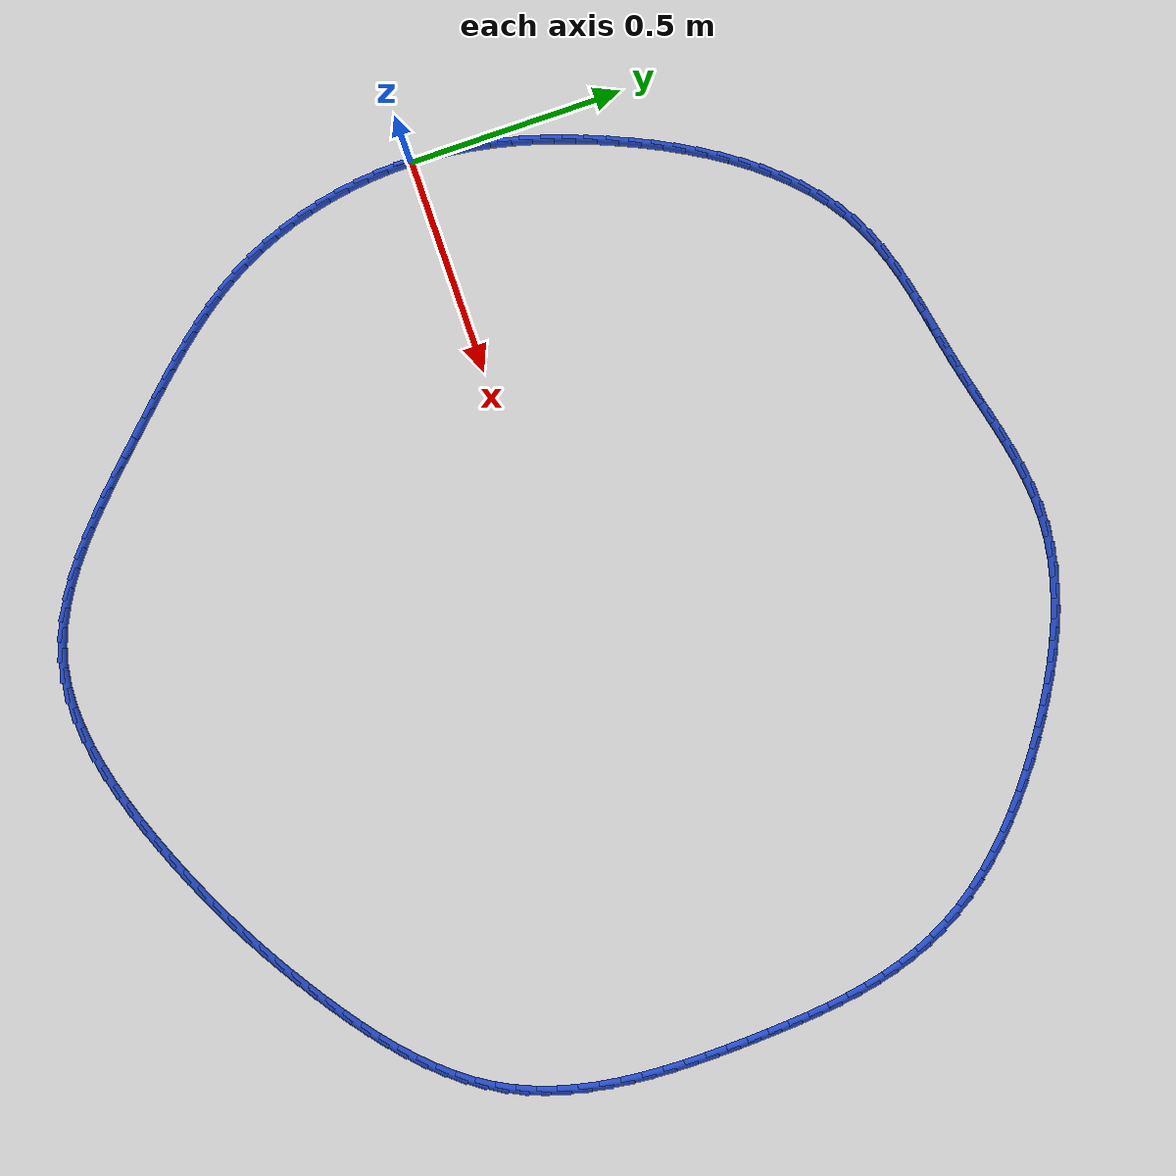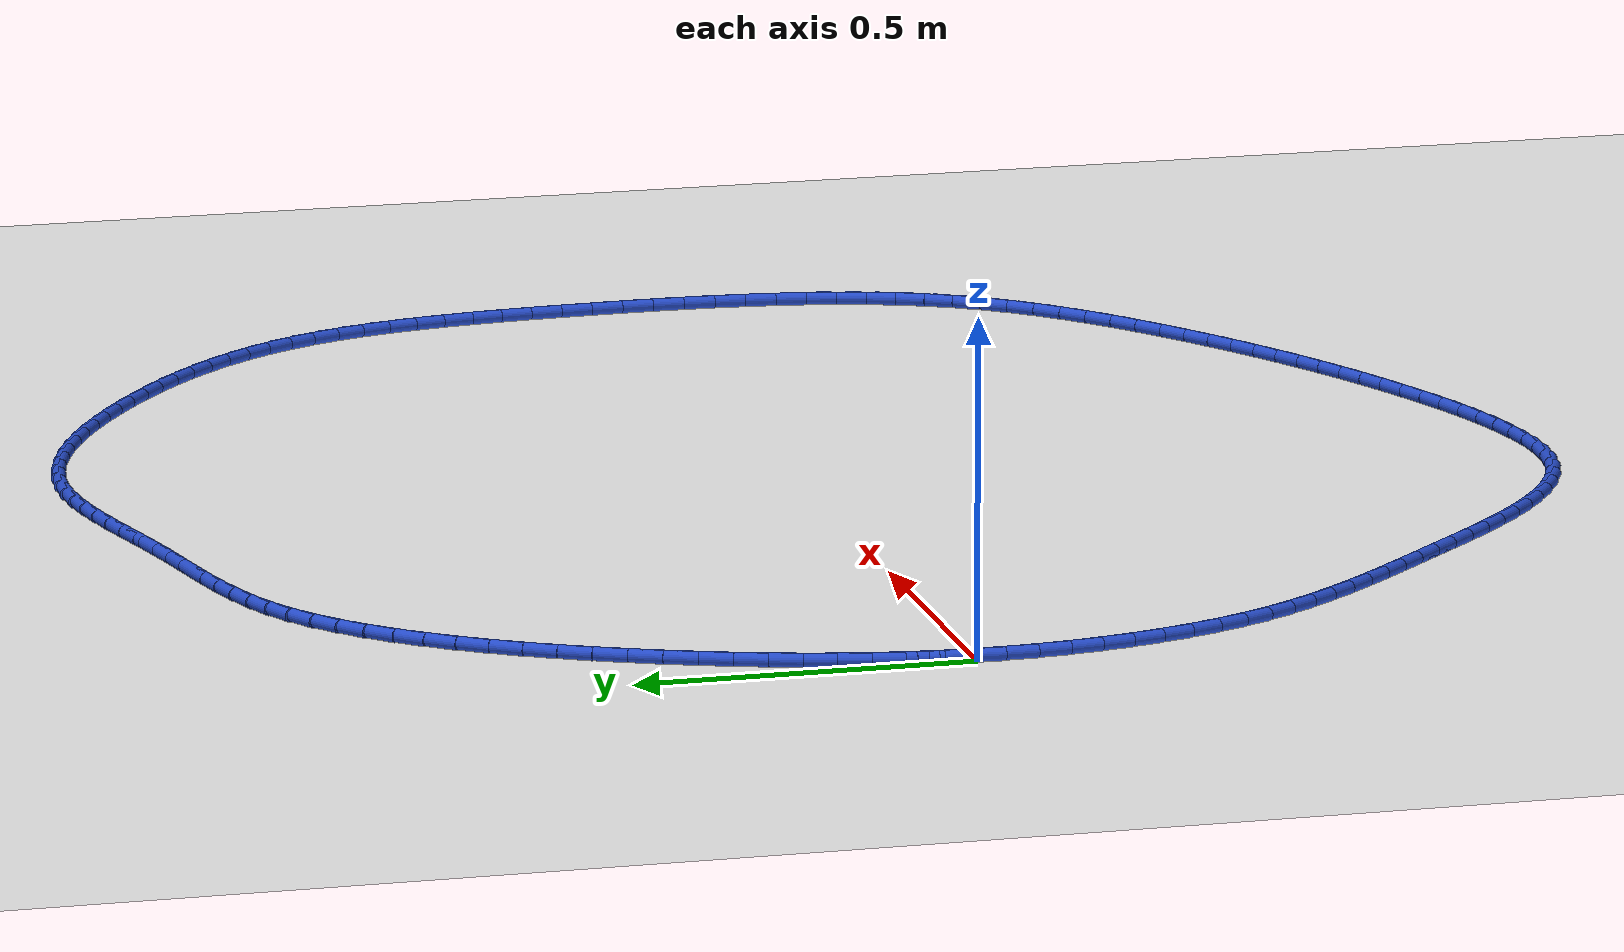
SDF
<sdf version="1.6">
 <world name="default">
  <light name="sun" type="directional">
   <pose>0 0 10 0 -0 0</pose>
   <diffuse>0.8 0.8 0.8 1</diffuse>
   <specular>0.2 0.2 0.2 1</specular>
   <attenuation>
    <range>1000</range>
    <constant>0.9</constant>
    <linear>0.01</linear>
    <quadratic>0.001</quadratic>
   </attenuation>
   <direction>-0.5 0.1 -0.9</direction>
  </light>
  <model name="ground_plane">
   <static>1</static>
   <link name="link">
    <collision name="collision">
     <geometry><plane><normal>0 0 1</normal><size>100 100</size></plane></geometry>
     <surface><friction><ode><mu>100</mu><mu2>50</mu2></ode></friction></surface>
    </collision>
    <visual name="visual">
     <cast_shadows>0</cast_shadows>
     <geometry><plane><normal>0 0 1</normal><size>100 100</size></plane></geometry>
     <material>
      <script><uri>file://media/materials/scripts/gazebo.material</uri><name>Gazebo/WhiteGlow</name></script>
     </material>
    </visual>
   </link>
  </model>
  <gravity>0 0 -9.8</gravity>
  <magnetic_field>6e-06 2.3e-05 -4.2e-05</magnetic_field>
  <atmosphere type="adiabatic"/>
  <physics name="default_physics" default="0" type="ode">
   <max_step_size>0.001</max_step_size>
   <real_time_factor>1</real_time_factor>
   <real_time_update_rate>1000</real_time_update_rate>
  </physics>
  <scene><ambient>0.4 0.4 0.4 1</ambient><background>0.7 0.7 0.7 1</background><shadows>1</shadows></scene>
  <spherical_coordinates>
   <surface_model>EARTH_WGS84</surface_model>
   <latitude_deg>0</latitude_deg>
   <longitude_deg>0</longitude_deg>
   <elevation>0</elevation>
   <heading_deg>0</heading_deg>
  </spherical_coordinates>
  <model name="line">
   <link name="link_0">
    <pose>4.5102810375396984e-17 -1.3877787807814457e-16 0.01 0 1.57 1.5298107565489703</pose>
    <collision name="collision">
     <geometry><cylinder><radius>0.01</radius><length>0.08</length></cylinder></geometry>
    </collision>
    <visual name="visual">
     <material>
      <script><name>Gazebo/Blue</name><uri>file://media/materials/scripts/gazebo.material</uri></script>
     </material>
     <geometry><cylinder><radius>0.01</radius><length>0.08</length></cylinder></geometry>
    </visual>
   </link>
   <link name="link_1">
    <pose>0.0019685583259757096 0.04800362464520385 0.01 0 1.57 1.479716273521104</pose>
    <collision name="collision">
     <geometry><cylinder><radius>0.01</radius><length>0.08</length></cylinder></geometry>
    </collision>
    <visual name="visual">
     <material>
      <script><name>Gazebo/Blue</name><uri>file://media/materials/scripts/gazebo.material</uri></script>
     </material>
     <geometry><cylinder><radius>0.01</radius><length>0.08</length></cylinder></geometry>
    </visual>
   </link>
   <link name="link_2">
    <pose>0.006317493180500105 0.09562000608899066 0.01 0 1.57 1.4316950958429615</pose>
    <collision name="collision">
     <geometry><cylinder><radius>0.01</radius><length>0.08</length></cylinder></geometry>
    </collision>
    <visual name="visual">
     <material>
      <script><name>Gazebo/Blue</name><uri>file://media/materials/scripts/gazebo.material</uri></script>
     </material>
     <geometry><cylinder><radius>0.01</radius><length>0.08</length></cylinder></geometry>
    </visual>
   </link>
   <link name="link_3">
    <pose>0.012936102183389237 0.14289396357088413 0.01 0 1.57 1.3860753619875683</pose>
    <collision name="collision">
     <geometry><cylinder><radius>0.01</radius><length>0.08</length></cylinder></geometry>
    </collision>
    <visual name="visual">
     <material>
      <script><name>Gazebo/Blue</name><uri>file://media/materials/scripts/gazebo.material</uri></script>
     </material>
     <geometry><cylinder><radius>0.01</radius><length>0.08</length></cylinder></geometry>
    </visual>
   </link>
   <link name="link_4">
    <pose>0.02171368295445912 0.18987031633040816 0.01 0 1.57 1.3431139589828611</pose>
    <collision name="collision">
     <geometry><cylinder><radius>0.01</radius><length>0.08</length></cylinder></geometry>
    </collision>
    <visual name="visual">
     <material>
      <script><name>Gazebo/Blue</name><uri>file://media/materials/scripts/gazebo.material</uri></script>
     </material>
     <geometry><cylinder><radius>0.01</radius><length>0.08</length></cylinder></geometry>
    </visual>
   </link>
   <link name="link_5">
    <pose>0.032539533113525775 0.23659388360708675 0.01 0 1.57 1.3029972884537147</pose>
    <collision name="collision">
     <geometry><cylinder><radius>0.01</radius><length>0.08</length></cylinder></geometry>
    </collision>
    <visual name="visual">
     <material>
      <script><name>Gazebo/Blue</name><uri>file://media/materials/scripts/gazebo.material</uri></script>
     </material>
     <geometry><cylinder><radius>0.01</radius><length>0.08</length></cylinder></geometry>
    </visual>
   </link>
   <link name="link_6">
    <pose>0.04530295028040521 0.2831094846404437 0.01 0 1.57 1.2658463277626237</pose>
    <collision name="collision">
     <geometry><cylinder><radius>0.01</radius><length>0.08</length></cylinder></geometry>
    </collision>
    <visual name="visual">
     <material>
      <script><name>Gazebo/Blue</name><uri>file://media/materials/scripts/gazebo.material</uri></script>
     </material>
     <geometry><cylinder><radius>0.01</radius><length>0.08</length></cylinder></geometry>
    </visual>
   </link>
   <link name="link_7">
    <pose>0.05989323207491339 0.32946193867000284 0.01 0 1.57 1.2317245821310854</pose>
    <collision name="collision">
     <geometry><cylinder><radius>0.01</radius><length>0.08</length></cylinder></geometry>
    </collision>
    <visual name="visual">
     <material>
      <script><name>Gazebo/Blue</name><uri>file://media/materials/scripts/gazebo.material</uri></script>
     </material>
     <geometry><cylinder><radius>0.01</radius><length>0.08</length></cylinder></geometry>
    </visual>
   </link>
   <link name="link_8">
    <pose>0.0761996761168664 0.3756960649352883 0.01 0 1.57 1.2006475588033874</pose>
    <collision name="collision">
     <geometry><cylinder><radius>0.01</radius><length>0.08</length></cylinder></geometry>
    </collision>
    <visual name="visual">
     <material>
      <script><name>Gazebo/Blue</name><uri>file://media/materials/scripts/gazebo.material</uri></script>
     </material>
     <geometry><cylinder><radius>0.01</radius><length>0.08</length></cylinder></geometry>
    </visual>
   </link>
   <link name="link_9">
    <pose>0.0941115800260802 0.42185668267582377 0.01 0 1.57 1.1722129539264694</pose>
    <collision name="collision">
     <geometry><cylinder><radius>0.01</radius><length>0.08</length></cylinder></geometry>
    </collision>
    <visual name="visual">
     <material>
      <script><name>Gazebo/Blue</name><uri>file://media/materials/scripts/gazebo.material</uri></script>
     </material>
     <geometry><cylinder><radius>0.01</radius><length>0.08</length></cylinder></geometry>
    </visual>
   </link>
   <link name="link_10">
    <pose>0.11352888065028877 0.46796491665800755 0.01 0 1.57 1.1428740697160042</pose>
    <collision name="collision">
     <geometry><cylinder><radius>0.01</radius><length>0.08</length></cylinder></geometry>
    </collision>
    <visual name="visual">
     <material>
      <script><name>Gazebo/Blue</name><uri>file://media/materials/scripts/gazebo.material</uri></script>
     </material>
     <geometry><cylinder><radius>0.01</radius><length>0.08</length></cylinder></geometry>
    </visual>
   </link>
   <link name="link_11">
    <pose>0.1344474933338868 0.5138281393038654 0.01 0 1.57 1.1104981738132114</pose>
    <collision name="collision">
     <geometry><cylinder><radius>0.01</radius><length>0.08</length></cylinder></geometry>
    </collision>
    <visual name="visual">
     <material>
      <script><name>Gazebo/Blue</name><uri>file://media/materials/scripts/gazebo.material</uri></script>
     </material>
     <geometry><cylinder><radius>0.01</radius><length>0.08</length></cylinder></geometry>
    </visual>
   </link>
   <link name="link_12">
    <pose>0.15691422144329 0.5591403910455921 0.01 0 1.57 1.0746743261360279</pose>
    <collision name="collision">
     <geometry><cylinder><radius>0.01</radius><length>0.08</length></cylinder></geometry>
    </collision>
    <visual name="visual">
     <material>
      <script><name>Gazebo/Blue</name><uri>file://media/materials/scripts/gazebo.material</uri></script>
     </material>
     <geometry><cylinder><radius>0.01</radius><length>0.08</length></cylinder></geometry>
    </visual>
   </link>
   <link name="link_13">
    <pose>0.18097633478914657 0.6035946735040698 0.01 0 1.57 1.034955410138871</pose>
    <collision name="collision">
     <geometry><cylinder><radius>0.01</radius><length>0.08</length></cylinder></geometry>
    </collision>
    <visual name="visual">
     <material>
      <script><name>Gazebo/Blue</name><uri>file://media/materials/scripts/gazebo.material</uri></script>
     </material>
     <geometry><cylinder><radius>0.01</radius><length>0.08</length></cylinder></geometry>
    </visual>
   </link>
   <link name="link_14">
    <pose>0.20668110318210464 0.6468839883001797 0.01 0 1.57 0.9908417420385939</pose>
    <collision name="collision">
     <geometry><cylinder><radius>0.01</radius><length>0.08</length></cylinder></geometry>
    </collision>
    <visual name="visual">
     <material>
      <script><name>Gazebo/Blue</name><uri>file://media/materials/scripts/gazebo.material</uri></script>
     </material>
     <geometry><cylinder><radius>0.01</radius><length>0.08</length></cylinder></geometry>
    </visual>
   </link>
   <link name="link_15">
    <pose>0.2340757964328125 0.6887013370548042 0.01 0 1.57 0.9417866814003238</pose>
    <collision name="collision">
     <geometry><cylinder><radius>0.01</radius><length>0.08</length></cylinder></geometry>
    </collision>
    <visual name="visual">
     <material>
      <script><name>Gazebo/Blue</name><uri>file://media/materials/scripts/gazebo.material</uri></script>
     </material>
     <geometry><cylinder><radius>0.01</radius><length>0.08</length></cylinder></geometry>
    </visual>
   </link>
   <link name="link_16">
    <pose>0.2632076843519182 0.7287397213888243 0.01 0 1.57 0.8872112230858543</pose>
    <collision name="collision">
     <geometry><cylinder><radius>0.01</radius><length>0.08</length></cylinder></geometry>
    </collision>
    <visual name="visual">
     <material>
      <script><name>Gazebo/Blue</name><uri>file://media/materials/scripts/gazebo.material</uri></script>
     </material>
     <geometry><cylinder><radius>0.01</radius><length>0.08</length></cylinder></geometry>
    </visual>
   </link>
   <link name="link_17">
    <pose>0.29412403675007 0.7666921429231219 0.01 0 1.57 0.8265325323151879</pose>
    <collision name="collision">
     <geometry><cylinder><radius>0.01</radius><length>0.08</length></cylinder></geometry>
    </collision>
    <visual name="visual">
     <material>
      <script><name>Gazebo/Blue</name><uri>file://media/materials/scripts/gazebo.material</uri></script>
     </material>
     <geometry><cylinder><radius>0.01</radius><length>0.08</length></cylinder></geometry>
    </visual>
   </link>
   <link name="link_18">
    <pose>0.3268721234379157 0.8022516032785786 0.01 0 1.57 0.7592124289744265</pose>
    <collision name="collision">
     <geometry><cylinder><radius>0.01</radius><length>0.08</length></cylinder></geometry>
    </collision>
    <visual name="visual">
     <material>
      <script><name>Gazebo/Blue</name><uri>file://media/materials/scripts/gazebo.material</uri></script>
     </material>
     <geometry><cylinder><radius>0.01</radius><length>0.08</length></cylinder></geometry>
    </visual>
   </link>
   <link name="link_19">
    <pose>0.36149921422610387 0.8351111040760759 0.01 0 1.57 0.684831558198611</pose>
    <collision name="collision">
     <geometry><cylinder><radius>0.01</radius><length>0.08</length></cylinder></geometry>
    </collision>
    <visual name="visual">
     <material>
      <script><name>Gazebo/Blue</name><uri>file://media/materials/scripts/gazebo.material</uri></script>
     </material>
     <geometry><cylinder><radius>0.01</radius><length>0.08</length></cylinder></geometry>
    </visual>
   </link>
   <link name="link_20">
    <pose>0.39805257892528256 0.8649636469364961 0.01 0 1.57 0.6031916091893048</pose>
    <collision name="collision">
     <geometry><cylinder><radius>0.01</radius><length>0.08</length></cylinder></geometry>
    </collision>
    <visual name="visual">
     <material>
      <script><name>Gazebo/Blue</name><uri>file://media/materials/scripts/gazebo.material</uri></script>
     </material>
     <geometry><cylinder><radius>0.01</radius><length>0.08</length></cylinder></geometry>
    </visual>
   </link>
   <link name="link_21">
    <pose>0.43657948734609997 0.8915022334807204 0.01 0 1.57 0.5144476279860516</pose>
    <collision name="collision">
     <geometry><cylinder><radius>0.01</radius><length>0.08</length></cylinder></geometry>
    </collision>
    <visual name="visual">
     <material>
      <script><name>Gazebo/Blue</name><uri>file://media/materials/scripts/gazebo.material</uri></script>
     </material>
     <geometry><cylinder><radius>0.01</radius><length>0.08</length></cylinder></geometry>
    </visual>
   </link>
   <link name="link_22">
    <pose>0.47712707361974827 0.914420237262024 0.01 0 1.57 0.42446266654170306</pose>
    <collision name="collision">
     <geometry><cylinder><radius>0.01</radius><length>0.08</length></cylinder></geometry>
    </collision>
    <visual name="visual">
     <material>
      <script><name>Gazebo/Blue</name><uri>file://media/materials/scripts/gazebo.material</uri></script>
     </material>
     <geometry><cylinder><radius>0.01</radius><length>0.08</length></cylinder></geometry>
    </visual>
   </link>
   <link name="link_23">
    <pose>0.519658344707158 0.9336416461125323 0.01 0 1.57 0.3483937999935151</pose>
    <collision name="collision">
     <geometry><cylinder><radius>0.01</radius><length>0.08</length></cylinder></geometry>
    </collision>
    <visual name="visual">
     <material>
      <script><name>Gazebo/Blue</name><uri>file://media/materials/scripts/gazebo.material</uri></script>
     </material>
     <geometry><cylinder><radius>0.01</radius><length>0.08</length></cylinder></geometry>
    </visual>
   </link>
   <link name="link_24">
    <pose>0.5639088901977909 0.9497138575541899 0.01 0 1.57 0.2889337930426981</pose>
    <collision name="collision">
     <geometry><cylinder><radius>0.01</radius><length>0.08</length></cylinder></geometry>
    </collision>
    <visual name="visual">
     <material>
      <script><name>Gazebo/Blue</name><uri>file://media/materials/scripts/gazebo.material</uri></script>
     </material>
     <geometry><cylinder><radius>0.01</radius><length>0.08</length></cylinder></geometry>
    </visual>
   </link>
   <link name="link_25">
    <pose>0.6095762504589655 0.9632885718436941 0.01 0 1.57 0.2456522877888159</pose>
    <collision name="collision">
     <geometry><cylinder><radius>0.01</radius><length>0.08</length></cylinder></geometry>
    </collision>
    <visual name="visual">
     <material>
      <script><name>Gazebo/Blue</name><uri>file://media/materials/scripts/gazebo.material</uri></script>
     </material>
     <geometry><cylinder><radius>0.01</radius><length>0.08</length></cylinder></geometry>
    </visual>
   </link>
   <link name="link_26">
    <pose>0.6563579658580011 0.9750174892377432 0.01 0 1.57 0.21783711492944408</pose>
    <collision name="collision">
     <geometry><cylinder><radius>0.01</radius><length>0.08</length></cylinder></geometry>
    </collision>
    <visual name="visual">
     <material>
      <script><name>Gazebo/Blue</name><uri>file://media/materials/scripts/gazebo.material</uri></script>
     </material>
     <geometry><cylinder><radius>0.01</radius><length>0.08</length></cylinder></geometry>
    </visual>
   </link>
   <link name="link_27">
    <pose>0.703951576762216 0.9855523099930336 0.01 0 1.57 0.20481665417565642</pose>
    <collision name="collision">
     <geometry><cylinder><radius>0.01</radius><length>0.08</length></cylinder></geometry>
    </collision>
    <visual name="visual">
     <material>
      <script><name>Gazebo/Blue</name><uri>file://media/materials/scripts/gazebo.material</uri></script>
     </material>
     <geometry><cylinder><radius>0.01</radius><length>0.08</length></cylinder></geometry>
    </visual>
   </link>
   <link name="link_28">
    <pose>0.7520546235389295 0.9955447343662636 0.01 0 1.57 0.20613208351510096</pose>
    <collision name="collision">
     <geometry><cylinder><radius>0.01</radius><length>0.08</length></cylinder></geometry>
    </collision>
    <visual name="visual">
     <material>
      <script><name>Gazebo/Blue</name><uri>file://media/materials/scripts/gazebo.material</uri></script>
     </material>
     <geometry><cylinder><radius>0.01</radius><length>0.08</length></cylinder></geometry>
    </visual>
   </link>
   <link name="link_29">
    <pose>0.8003646465554598 1.0056464626141302 0.01 0 1.57 0.22142872966596028</pose>
    <collision name="collision">
     <geometry><cylinder><radius>0.01</radius><length>0.08</length></cylinder></geometry>
    </collision>
    <visual name="visual">
     <material>
      <script><name>Gazebo/Blue</name><uri>file://media/materials/scripts/gazebo.material</uri></script>
     </material>
     <geometry><cylinder><radius>0.01</radius><length>0.08</length></cylinder></geometry>
    </visual>
   </link>
   <link name="link_30">
    <pose>0.8485812869021407 1.0165009963631741 0.01 0 1.57 0.2407440698350381</pose>
    <collision name="collision">
     <geometry><cylinder><radius>0.01</radius><length>0.08</length></cylinder></geometry>
    </collision>
    <visual name="visual">
     <material>
      <script><name>Gazebo/Blue</name><uri>file://media/materials/scripts/gazebo.material</uri></script>
     </material>
     <geometry><cylinder><radius>0.01</radius><length>0.08</length></cylinder></geometry>
    </visual>
   </link>
   <link name="link_31">
    <pose>0.8965271422721968 1.0282719664024116 0.01 0 1.57 0.2487735495055872</pose>
    <collision name="collision">
     <geometry><cylinder><radius>0.01</radius><length>0.08</length></cylinder></geometry>
    </collision>
    <visual name="visual">
     <material>
      <script><name>Gazebo/Blue</name><uri>file://media/materials/scripts/gazebo.material</uri></script>
     </material>
     <geometry><cylinder><radius>0.01</radius><length>0.08</length></cylinder></geometry>
    </visual>
   </link>
   <link name="link_32">
    <pose>0.9442136390724715 1.0403860492555161 0.01 0 1.57 0.24413796565367507</pose>
    <collision name="collision">
     <geometry><cylinder><radius>0.01</radius><length>0.08</length></cylinder></geometry>
    </collision>
    <visual name="visual">
     <material>
      <script><name>Gazebo/Blue</name><uri>file://media/materials/scripts/gazebo.material</uri></script>
     </material>
     <geometry><cylinder><radius>0.01</radius><length>0.08</length></cylinder></geometry>
    </visual>
   </link>
   <link name="link_33">
    <pose>0.9916682437509212 1.0522073209205953 0.01 0 1.57 0.2265707509667855</pose>
    <collision name="collision">
     <geometry><cylinder><radius>0.01</radius><length>0.08</length></cylinder></geometry>
    </collision>
    <visual name="visual">
     <material>
      <script><name>Gazebo/Blue</name><uri>file://media/materials/scripts/gazebo.material</uri></script>
     </material>
     <geometry><cylinder><radius>0.01</radius><length>0.08</length></cylinder></geometry>
    </visual>
   </link>
   <link name="link_34">
    <pose>1.0389184227555015 1.0630998573957577 0.01 0 1.57 0.19562259872470217</pose>
    <collision name="collision">
     <geometry><cylinder><radius>0.01</radius><length>0.08</length></cylinder></geometry>
    </collision>
    <visual name="visual">
     <material>
      <script><name>Gazebo/Blue</name><uri>file://media/materials/scripts/gazebo.material</uri></script>
     </material>
     <geometry><cylinder><radius>0.01</radius><length>0.08</length></cylinder></geometry>
    </visual>
   </link>
   <link name="link_35">
    <pose>1.085991642534169 1.072427734679112 0.01 0 1.57 0.1507388686850639</pose>
    <collision name="collision">
     <geometry><cylinder><radius>0.01</radius><length>0.08</length></cylinder></geometry>
    </collision>
    <visual name="visual">
     <material>
      <script><name>Gazebo/Blue</name><uri>file://media/materials/scripts/gazebo.material</uri></script>
     </material>
     <geometry><cylinder><radius>0.01</radius><length>0.08</length></cylinder></geometry>
    </visual>
   </link>
   <link name="link_36">
    <pose>1.1329153695348793 1.0795550287687663 0.01 0 1.57 0.0914245718982712</pose>
    <collision name="collision">
     <geometry><cylinder><radius>0.01</radius><length>0.08</length></cylinder></geometry>
    </collision>
    <visual name="visual">
     <material>
      <script><name>Gazebo/Blue</name><uri>file://media/materials/scripts/gazebo.material</uri></script>
     </material>
     <geometry><cylinder><radius>0.01</radius><length>0.08</length></cylinder></geometry>
    </visual>
   </link>
   <link name="link_37">
    <pose>1.179717070205589 1.0838458156628292 0.01 0 1.57 0.017519315064775456</pose>
    <collision name="collision">
     <geometry><cylinder><radius>0.01</radius><length>0.08</length></cylinder></geometry>
    </collision>
    <visual name="visual">
     <material>
      <script><name>Gazebo/Blue</name><uri>file://media/materials/scripts/gazebo.material</uri></script>
     </material>
     <geometry><cylinder><radius>0.01</radius><length>0.08</length></cylinder></geometry>
    </visual>
   </link>
   <link name="link_38">
    <pose>1.2264242104224634 1.0846641764952913 0.01 0 1.57 -0.06683782724828961</pose>
    <collision name="collision">
     <geometry><cylinder><radius>0.01</radius><length>0.08</length></cylinder></geometry>
    </collision>
    <visual name="visual">
     <material>
      <script><name>Gazebo/Blue</name><uri>file://media/materials/scripts/gazebo.material</uri></script>
     </material>
     <geometry><cylinder><radius>0.01</radius><length>0.08</length></cylinder></geometry>
    </visual>
   </link>
   <link name="link_39">
    <pose>1.2730454101575142 1.081543468375305 0.01 0 1.57 -0.14763272213773246</pose>
    <collision name="collision">
     <geometry><cylinder><radius>0.01</radius><length>0.08</length></cylinder></geometry>
    </collision>
    <visual name="visual">
     <material>
      <script><name>Gazebo/Blue</name><uri>file://media/materials/scripts/gazebo.material</uri></script>
     </material>
     <geometry><cylinder><radius>0.01</radius><length>0.08</length></cylinder></geometry>
    </visual>
   </link>
   <link name="link_40">
    <pose>1.3195208378295624 1.07463188775973 0.01 0 1.57 -0.22146857922194682</pose>
    <collision name="collision">
     <geometry><cylinder><radius>0.01</radius><length>0.08</length></cylinder></geometry>
    </collision>
    <visual name="visual">
     <material>
      <script><name>Gazebo/Blue</name><uri>file://media/materials/scripts/gazebo.material</uri></script>
     </material>
     <geometry><cylinder><radius>0.01</radius><length>0.08</length></cylinder></geometry>
    </visual>
   </link>
   <link name="link_41">
    <pose>1.3657751252735757 1.0642171824032058 0.01 0 1.57 -0.28831471859771907</pose>
    <collision name="collision">
     <geometry><cylinder><radius>0.01</radius><length>0.08</length></cylinder></geometry>
    </collision>
    <visual name="visual">
     <material>
      <script><name>Gazebo/Blue</name><uri>file://media/materials/scripts/gazebo.material</uri></script>
     </material>
     <geometry><cylinder><radius>0.01</radius><length>0.08</length></cylinder></geometry>
    </visual>
   </link>
   <link name="link_42">
    <pose>1.4117329043245213 1.0505871000603713 0.01 0 1.57 -0.3484032185698907</pose>
    <collision name="collision">
     <geometry><cylinder><radius>0.01</radius><length>0.08</length></cylinder></geometry>
    </collision>
    <visual name="visual">
     <material>
      <script><name>Gazebo/Blue</name><uri>file://media/materials/scripts/gazebo.material</uri></script>
     </material>
     <geometry><cylinder><radius>0.01</radius><length>0.08</length></cylinder></geometry>
    </visual>
   </link>
   <link name="link_43">
    <pose>1.4573188068173657 1.034029388485865 0.01 0 1.57 -0.40212700964414694</pose>
    <collision name="collision">
     <geometry><cylinder><radius>0.01</radius><length>0.08</length></cylinder></geometry>
    </collision>
    <visual name="visual">
     <material>
      <script><name>Gazebo/Blue</name><uri>file://media/materials/scripts/gazebo.material</uri></script>
     </material>
     <geometry><cylinder><radius>0.01</radius><length>0.08</length></cylinder></geometry>
    </visual>
   </link>
   <link name="link_44">
    <pose>1.5024574645870772 1.0148317954343251 0.01 0 1.57 -0.44995857005328366</pose>
    <collision name="collision">
     <geometry><cylinder><radius>0.01</radius><length>0.08</length></cylinder></geometry>
    </collision>
    <visual name="visual">
     <material>
      <script><name>Gazebo/Blue</name><uri>file://media/materials/scripts/gazebo.material</uri></script>
     </material>
     <geometry><cylinder><radius>0.01</radius><length>0.08</length></cylinder></geometry>
    </visual>
   </link>
   <link name="link_45">
    <pose>1.547073509468622 0.9932820686603919 0.01 0 1.57 -0.4923916358469921</pose>
    <collision name="collision">
     <geometry><cylinder><radius>0.01</radius><length>0.08</length></cylinder></geometry>
    </collision>
    <visual name="visual">
     <material>
      <script><name>Gazebo/Blue</name><uri>file://media/materials/scripts/gazebo.material</uri></script>
     </material>
     <geometry><cylinder><radius>0.01</radius><length>0.08</length></cylinder></geometry>
    </visual>
   </link>
   <link name="link_46">
    <pose>1.591091573296969 0.9696679559187029 0.01 0 1.57 -0.5299028755190982</pose>
    <collision name="collision">
     <geometry><cylinder><radius>0.01</radius><length>0.08</length></cylinder></geometry>
    </collision>
    <visual name="visual">
     <material>
      <script><name>Gazebo/Blue</name><uri>file://media/materials/scripts/gazebo.material</uri></script>
     </material>
     <geometry><cylinder><radius>0.01</radius><length>0.08</length></cylinder></geometry>
    </visual>
   </link>
   <link name="link_47">
    <pose>1.6344362879070837 0.9442772049638978 0.01 0 1.57 -0.5629286055693025</pose>
    <collision name="collision">
     <geometry><cylinder><radius>0.01</radius><length>0.08</length></cylinder></geometry>
    </collision>
    <visual name="visual">
     <material>
      <script><name>Gazebo/Blue</name><uri>file://media/materials/scripts/gazebo.material</uri></script>
     </material>
     <geometry><cylinder><radius>0.01</radius><length>0.08</length></cylinder></geometry>
    </visual>
   </link>
   <link name="link_48">
    <pose>1.6770322851339343 0.9173975635506145 0.01 0 1.57 -0.592868454049372</pose>
    <collision name="collision">
     <geometry><cylinder><radius>0.01</radius><length>0.08</length></cylinder></geometry>
    </collision>
    <visual name="visual">
     <material>
      <script><name>Gazebo/Blue</name><uri>file://media/materials/scripts/gazebo.material</uri></script>
     </material>
     <geometry><cylinder><radius>0.01</radius><length>0.08</length></cylinder></geometry>
    </visual>
   </link>
   <link name="link_49">
    <pose>1.7187816655649688 0.8892702525024343 0.01 0 1.57 -0.6246684169122455</pose>
    <collision name="collision">
     <geometry><cylinder><radius>0.01</radius><length>0.08</length></cylinder></geometry>
    </collision>
    <visual name="visual">
     <material>
      <script><name>Gazebo/Blue</name><uri>file://media/materials/scripts/gazebo.material</uri></script>
     </material>
     <geometry><cylinder><radius>0.01</radius><length>0.08</length></cylinder></geometry>
    </visual>
   </link>
   <link name="link_50">
    <pose>1.7594839637620485 0.8599246942328679 0.01 0 1.57 -0.6599403322201002</pose>
    <collision name="collision">
     <geometry><cylinder><radius>0.01</radius><length>0.08</length></cylinder></geometry>
    </collision>
    <visual name="visual">
     <material>
      <script><name>Gazebo/Blue</name><uri>file://media/materials/scripts/gazebo.material</uri></script>
     </material>
     <geometry><cylinder><radius>0.01</radius><length>0.08</length></cylinder></geometry>
    </visual>
   </link>
   <link name="link_51">
    <pose>1.7989095448127657 0.8293300763141392 0.01 0 1.57 -0.6990051994394199</pose>
    <collision name="collision">
     <geometry><cylinder><radius>0.01</radius><length>0.08</length></cylinder></geometry>
    </collision>
    <visual name="visual">
     <material>
      <script><name>Gazebo/Blue</name><uri>file://media/materials/scripts/gazebo.material</uri></script>
     </material>
     <geometry><cylinder><radius>0.01</radius><length>0.08</length></cylinder></geometry>
    </visual>
   </link>
   <link name="link_52">
    <pose>1.8368287717523486 0.7974555820803487 0.01 0 1.57 -0.7422058300582275</pose>
    <collision name="collision">
     <geometry><cylinder><radius>0.01</radius><length>0.08</length></cylinder></geometry>
    </collision>
    <visual name="visual">
     <material>
      <script><name>Gazebo/Blue</name><uri>file://media/materials/scripts/gazebo.material</uri></script>
     </material>
     <geometry><cylinder><radius>0.01</radius><length>0.08</length></cylinder></geometry>
    </visual>
   </link>
   <link name="link_53">
    <pose>1.8730120076160273 0.7642703948655989 0.01 0 1.57 -0.7898943461315423</pose>
    <collision name="collision">
     <geometry><cylinder><radius>0.01</radius><length>0.08</length></cylinder></geometry>
    </collision>
    <visual name="visual">
     <material>
      <script><name>Gazebo/Blue</name><uri>file://media/materials/scripts/gazebo.material</uri></script>
     </material>
     <geometry><cylinder><radius>0.01</radius><length>0.08</length></cylinder></geometry>
    </visual>
   </link>
   <link name="link_54">
    <pose>1.9072296154390294 0.7297436980039909 0.01 0 1.57 -0.8424123129243463</pose>
    <collision name="collision">
     <geometry><cylinder><radius>0.01</radius><length>0.08</length></cylinder></geometry>
    </collision>
    <visual name="visual">
     <material>
      <script><name>Gazebo/Blue</name><uri>file://media/materials/scripts/gazebo.material</uri></script>
     </material>
     <geometry><cylinder><radius>0.01</radius><length>0.08</length></cylinder></geometry>
    </visual>
   </link>
   <link name="link_55">
    <pose>1.9392519582565848 0.6938446748296261 0.01 0 1.57 -0.9000614569259268</pose>
    <collision name="collision">
     <geometry><cylinder><radius>0.01</radius><length>0.08</length></cylinder></geometry>
    </collision>
    <visual name="visual">
     <material>
      <script><name>Gazebo/Blue</name><uri>file://media/materials/scripts/gazebo.material</uri></script>
     </material>
     <geometry><cylinder><radius>0.01</radius><length>0.08</length></cylinder></geometry>
    </visual>
   </link>
   <link name="link_56">
    <pose>1.9688493991039215 0.6565425086766066 0.01 0 1.57 -0.9630633681854971</pose>
    <collision name="collision">
     <geometry><cylinder><radius>0.01</radius><length>0.08</length></cylinder></geometry>
    </collision>
    <visual name="visual">
     <material>
      <script><name>Gazebo/Blue</name><uri>file://media/materials/scripts/gazebo.material</uri></script>
     </material>
     <geometry><cylinder><radius>0.01</radius><length>0.08</length></cylinder></geometry>
    </visual>
   </link>
   <link name="link_57">
    <pose>1.9957923010162693 0.6178063828790332 0.01 0 1.57 -1.0315082246874758</pose>
    <collision name="collision">
     <geometry><cylinder><radius>0.01</radius><length>0.08</length></cylinder></geometry>
    </collision>
    <visual name="visual">
     <material>
      <script><name>Gazebo/Blue</name><uri>file://media/materials/scripts/gazebo.material</uri></script>
     </material>
     <geometry><cylinder><radius>0.01</radius><length>0.08</length></cylinder></geometry>
    </visual>
   </link>
   <link name="link_58">
    <pose>2.0198510270288548 0.5776054807710082 0.01 0 1.57 -1.1051718665667225</pose>
    <collision name="collision">
     <geometry><cylinder><radius>0.01</radius><length>0.08</length></cylinder></geometry>
    </collision>
    <visual name="visual">
     <material>
      <script><name>Gazebo/Blue</name><uri>file://media/materials/scripts/gazebo.material</uri></script>
     </material>
     <geometry><cylinder><radius>0.01</radius><length>0.08</length></cylinder></geometry>
    </visual>
   </link>
   <link name="link_59">
    <pose>2.040801517119994 0.5359107653581479 0.01 0 1.57 -1.1789438649446577</pose>
    <collision name="collision">
     <geometry><cylinder><radius>0.01</radius><length>0.08</length></cylinder></geometry>
    </collision>
    <visual name="visual">
     <material>
      <script><name>Gazebo/Blue</name><uri>file://media/materials/scripts/gazebo.material</uri></script>
     </material>
     <geometry><cylinder><radius>0.01</radius><length>0.08</length></cylinder></geometry>
    </visual>
   </link>
   <link name="link_60">
    <pose>2.0586319771949984 0.49276093632874063 0.01 0 1.57 -1.246106195046439</pose>
    <collision name="collision">
     <geometry><cylinder><radius>0.01</radius><length>0.08</length></cylinder></geometry>
    </collision>
    <visual name="visual">
     <material>
      <script><name>Gazebo/Blue</name><uri>file://media/materials/scripts/gazebo.material</uri></script>
     </material>
     <geometry><cylinder><radius>0.01</radius><length>0.08</length></cylinder></geometry>
    </visual>
   </link>
   <link name="link_61">
    <pose>2.0736037573040944 0.4482818570460393 0.01 0 1.57 -1.3058660643151485</pose>
    <collision name="collision">
     <geometry><cylinder><radius>0.01</radius><length>0.08</length></cylinder></geometry>
    </collision>
    <visual name="visual">
     <material>
      <script><name>Gazebo/Blue</name><uri>file://media/materials/scripts/gazebo.material</uri></script>
     </material>
     <geometry><cylinder><radius>0.01</radius><length>0.08</length></cylinder></geometry>
    </visual>
   </link>
   <link name="link_62">
    <pose>2.085996203288407 0.40260513355275124 0.01 0 1.57 -1.3581458747196922</pose>
    <collision name="collision">
     <geometry><cylinder><radius>0.01</radius><length>0.08</length></cylinder></geometry>
    </collision>
    <visual name="visual">
     <material>
      <script><name>Gazebo/Blue</name><uri>file://media/materials/scripts/gazebo.material</uri></script>
     </material>
     <geometry><cylinder><radius>0.01</radius><length>0.08</length></cylinder></geometry>
    </visual>
   </link>
   <link name="link_63">
    <pose>2.096088660989064 0.3558623718915824 0.01 0 1.57 -1.4030852335873243</pose>
    <collision name="collision">
     <geometry><cylinder><radius>0.01</radius><length>0.08</length></cylinder></geometry>
    </collision>
    <visual name="visual">
     <material>
      <script><name>Gazebo/Blue</name><uri>file://media/materials/scripts/gazebo.material</uri></script>
     </material>
     <geometry><cylinder><radius>0.01</radius><length>0.08</length></cylinder></geometry>
    </visual>
   </link>
   <link name="link_64">
    <pose>2.1041604762471895 0.30818517810524004 0.01 0 1.57 -1.4409510516075943</pose>
    <collision name="collision">
     <geometry><cylinder><radius>0.01</radius><length>0.08</length></cylinder></geometry>
    </collision>
    <visual name="visual">
     <material>
      <script><name>Gazebo/Blue</name><uri>file://media/materials/scripts/gazebo.material</uri></script>
     </material>
     <geometry><cylinder><radius>0.01</radius><length>0.08</length></cylinder></geometry>
    </visual>
   </link>
   <link name="link_65">
    <pose>2.110490994903911 0.25970515823643064 0.01 0 1.57 -1.4720655845754989</pose>
    <collision name="collision">
     <geometry><cylinder><radius>0.01</radius><length>0.08</length></cylinder></geometry>
    </collision>
    <visual name="visual">
     <material>
      <script><name>Gazebo/Blue</name><uri>file://media/materials/scripts/gazebo.material</uri></script>
     </material>
     <geometry><cylinder><radius>0.01</radius><length>0.08</length></cylinder></geometry>
    </visual>
   </link>
   <link name="link_66">
    <pose>2.1153595628003523 0.21055391832786036 0.01 0 1.57 -1.4967540348777757</pose>
    <collision name="collision">
     <geometry><cylinder><radius>0.01</radius><length>0.08</length></cylinder></geometry>
    </collision>
    <visual name="visual">
     <material>
      <script><name>Gazebo/Blue</name><uri>file://media/materials/scripts/gazebo.material</uri></script>
     </material>
     <geometry><cylinder><radius>0.01</radius><length>0.08</length></cylinder></geometry>
    </visual>
   </link>
   <link name="link_67">
    <pose>2.1190455257776417 0.16086306442223658 0.01 0 1.57 -1.5153090885168579</pose>
    <collision name="collision">
     <geometry><cylinder><radius>0.01</radius><length>0.08</length></cylinder></geometry>
    </collision>
    <visual name="visual">
     <material>
      <script><name>Gazebo/Blue</name><uri>file://media/materials/scripts/gazebo.material</uri></script>
     </material>
     <geometry><cylinder><radius>0.01</radius><length>0.08</length></cylinder></geometry>
    </visual>
   </link>
   <link name="link_68">
    <pose>2.121828229676903 0.11076420256226528 0.01 0 1.57 -1.5281952262705571</pose>
    <collision name="collision">
     <geometry><cylinder><radius>0.01</radius><length>0.08</length></cylinder></geometry>
    </collision>
    <visual name="visual">
     <material>
      <script><name>Gazebo/Blue</name><uri>file://media/materials/scripts/gazebo.material</uri></script>
     </material>
     <geometry><cylinder><radius>0.01</radius><length>0.08</length></cylinder></geometry>
    </visual>
   </link>
   <link name="link_69">
    <pose>2.1239755420799225 0.06038960659933465 0.01 0 1.57 -1.5406486295381716</pose>
    <collision name="collision">
     <geometry><cylinder><radius>0.01</radius><length>0.08</length></cylinder></geometry>
    </collision>
    <visual name="visual">
     <material>
      <script><name>Gazebo/Blue</name><uri>file://media/materials/scripts/gazebo.material</uri></script>
     </material>
     <geometry><cylinder><radius>0.01</radius><length>0.08</length></cylinder></geometry>
    </visual>
   </link>
   <link name="link_70">
    <pose>2.1254985562040076 0.00988648959682385 0.01 0 1.57 -1.557779633722031</pose>
    <collision name="collision">
     <geometry><cylinder><radius>0.01</radius><length>0.08</length></cylinder></geometry>
    </collision>
    <visual name="visual">
     <material>
      <script><name>Gazebo/Blue</name><uri>file://media/materials/scripts/gazebo.material</uri></script>
     </material>
     <geometry><cylinder><radius>0.01</radius><length>0.08</length></cylinder></geometry>
    </visual>
   </link>
   <link name="link_71">
    <pose>2.126155542107821 -0.04058322605227191 0.01 0 1.57 1.5616176386527165</pose>
    <collision name="collision">
     <geometry><cylinder><radius>0.01</radius><length>0.08</length></cylinder></geometry>
    </collision>
    <visual name="visual">
     <material>
      <script><name>Gazebo/Blue</name><uri>file://media/materials/scripts/gazebo.material</uri></script>
     </material>
     <geometry><cylinder><radius>0.01</radius><length>0.08</length></cylinder></geometry>
    </visual>
   </link>
   <link name="link_72">
    <pose>2.125694081891426 -0.09085699612621957 0.01 0 1.57 1.534104118408321</pose>
    <collision name="collision">
     <geometry><cylinder><radius>0.01</radius><length>0.08</length></cylinder></geometry>
    </collision>
    <visual name="visual">
     <material>
      <script><name>Gazebo/Blue</name><uri>file://media/materials/scripts/gazebo.material</uri></script>
     </material>
     <geometry><cylinder><radius>0.01</radius><length>0.08</length></cylinder></geometry>
    </visual>
   </link>
   <link name="link_73">
    <pose>2.1238617576548817 -0.14077227640328635 0.01 0 1.57 1.500950438704793</pose>
    <collision name="collision">
     <geometry><cylinder><radius>0.01</radius><length>0.08</length></cylinder></geometry>
    </collision>
    <visual name="visual">
     <material>
      <script><name>Gazebo/Blue</name><uri>file://media/materials/scripts/gazebo.material</uri></script>
     </material>
     <geometry><cylinder><radius>0.01</radius><length>0.08</length></cylinder></geometry>
    </visual>
   </link>
   <link name="link_74">
    <pose>2.1204061514982513 -0.19016652266173714 0.01 0 1.57 1.4617818117217025</pose>
    <collision name="collision">
     <geometry><cylinder><radius>0.01</radius><length>0.08</length></cylinder></geometry>
    </collision>
    <visual name="visual">
     <material>
      <script><name>Gazebo/Blue</name><uri>file://media/materials/scripts/gazebo.material</uri></script>
     </material>
     <geometry><cylinder><radius>0.01</radius><length>0.08</length></cylinder></geometry>
    </visual>
   </link>
   <link name="link_75">
    <pose>2.1150748455215966 -0.23887719067983923 0.01 0 1.57 1.4161954958157235</pose>
    <collision name="collision">
     <geometry><cylinder><radius>0.01</radius><length>0.08</length></cylinder></geometry>
    </collision>
    <visual name="visual">
     <material>
      <script><name>Gazebo/Blue</name><uri>file://media/materials/scripts/gazebo.material</uri></script>
     </material>
     <geometry><cylinder><radius>0.01</radius><length>0.08</length></cylinder></geometry>
    </visual>
   </link>
   <link name="link_76">
    <pose>2.107615421824979 -0.28674173623585913 0.01 0 1.57 1.3637995384842094</pose>
    <collision name="collision">
     <geometry><cylinder><radius>0.01</radius><length>0.08</length></cylinder></geometry>
    </collision>
    <visual name="visual">
     <material>
      <script><name>Gazebo/Blue</name><uri>file://media/materials/scripts/gazebo.material</uri></script>
     </material>
     <geometry><cylinder><radius>0.01</radius><length>0.08</length></cylinder></geometry>
    </visual>
   </link>
   <link name="link_77">
    <pose>2.097775462508461 -0.33359761510806335 0.01 0 1.57 1.304270109160531</pose>
    <collision name="collision">
     <geometry><cylinder><radius>0.01</radius><length>0.08</length></cylinder></geometry>
    </collision>
    <visual name="visual">
     <material>
      <script><name>Gazebo/Blue</name><uri>file://media/materials/scripts/gazebo.material</uri></script>
     </material>
     <geometry><cylinder><radius>0.01</radius><length>0.08</length></cylinder></geometry>
    </visual>
   </link>
   <link name="link_78">
    <pose>2.085302549672104 -0.3792822830747189 0.01 0 1.57 1.2374303117309948</pose>
    <collision name="collision">
     <geometry><cylinder><radius>0.01</radius><length>0.08</length></cylinder></geometry>
    </collision>
    <visual name="visual">
     <material>
      <script><name>Gazebo/Blue</name><uri>file://media/materials/scripts/gazebo.material</uri></script>
     </material>
     <geometry><cylinder><radius>0.01</radius><length>0.08</length></cylinder></geometry>
    </visual>
   </link>
   <link name="link_79">
    <pose>2.0699442654159705 -0.4236331959140911 0.01 0 1.57 1.1633482874820653</pose>
    <collision name="collision">
     <geometry><cylinder><radius>0.01</radius><length>0.08</length></cylinder></geometry>
    </collision>
    <visual name="visual">
     <material>
      <script><name>Gazebo/Blue</name><uri>file://media/materials/scripts/gazebo.material</uri></script>
     </material>
     <geometry><cylinder><radius>0.01</radius><length>0.08</length></cylinder></geometry>
    </visual>
   </link>
   <link name="link_80">
    <pose>2.0514481918401213 -0.466487809404447 0.01 0 1.57 1.0824429496278638</pose>
    <collision name="collision">
     <geometry><cylinder><radius>0.01</radius><length>0.08</length></cylinder></geometry>
    </collision>
    <visual name="visual">
     <material>
      <script><name>Gazebo/Blue</name><uri>file://media/materials/scripts/gazebo.material</uri></script>
     </material>
     <geometry><cylinder><radius>0.01</radius><length>0.08</length></cylinder></geometry>
    </visual>
   </link>
   <link name="link_81">
    <pose>2.0295619126116384 -0.5076835799189534 0.01 0 1.57 0.9981407344268346</pose>
    <collision name="collision">
     <geometry><cylinder><radius>0.01</radius><length>0.08</length></cylinder></geometry>
    </collision>
    <visual name="visual">
     <material>
      <script><name>Gazebo/Blue</name><uri>file://media/materials/scripts/gazebo.material</uri></script>
     </material>
     <geometry><cylinder><radius>0.01</radius><length>0.08</length></cylinder></geometry>
    </visual>
   </link>
   <link name="link_82">
    <pose>2.0041482035846974 -0.547101695192288 0.01 0 1.57 0.9207548499879681</pose>
    <collision name="collision">
     <geometry><cylinder><radius>0.01</radius><length>0.08</length></cylinder></geometry>
    </collision>
    <visual name="visual">
     <material>
      <script><name>Gazebo/Blue</name><uri>file://media/materials/scripts/gazebo.material</uri></script>
     </material>
     <geometry><cylinder><radius>0.01</radius><length>0.08</length></cylinder></geometry>
    </visual>
   </link>
   <link name="link_83">
    <pose>1.9754980369084643 -0.5847859026556256 0.01 0 1.57 0.8524641445979597</pose>
    <collision name="collision">
     <geometry><cylinder><radius>0.01</radius><length>0.08</length></cylinder></geometry>
    </collision>
    <visual name="visual">
     <material>
      <script><name>Gazebo/Blue</name><uri>file://media/materials/scripts/gazebo.material</uri></script>
     </material>
     <geometry><cylinder><radius>0.01</radius><length>0.08</length></cylinder></geometry>
    </visual>
   </link>
   <link name="link_84">
    <pose>1.9440018587713128 -0.6208177138913336 0.01 0 1.57 0.7928408458551787</pose>
    <collision name="collision">
     <geometry><cylinder><radius>0.01</radius><length>0.08</length></cylinder></geometry>
    </collision>
    <visual name="visual">
     <material>
      <script><name>Gazebo/Blue</name><uri>file://media/materials/scripts/gazebo.material</uri></script>
     </material>
     <geometry><cylinder><radius>0.01</radius><length>0.08</length></cylinder></geometry>
    </visual>
   </link>
   <link name="link_85">
    <pose>1.9100501153616152 -0.6552786404817791 0.01 0 1.57 0.741284477686743</pose>
    <collision name="collision">
     <geometry><cylinder><radius>0.01</radius><length>0.08</length></cylinder></geometry>
    </collision>
    <visual name="visual">
     <material>
      <script><name>Gazebo/Blue</name><uri>file://media/materials/scripts/gazebo.material</uri></script>
     </material>
     <geometry><cylinder><radius>0.01</radius><length>0.08</length></cylinder></geometry>
    </visual>
   </link>
   <link name="link_86">
    <pose>1.8740332528677472 -0.6882501940093289 0.01 0 1.57 0.6971459620865529</pose>
    <collision name="collision">
     <geometry><cylinder><radius>0.01</radius><length>0.08</length></cylinder></geometry>
    </collision>
    <visual name="visual">
     <material>
      <script><name>Gazebo/Blue</name><uri>file://media/materials/scripts/gazebo.material</uri></script>
     </material>
     <geometry><cylinder><radius>0.01</radius><length>0.08</length></cylinder></geometry>
    </visual>
   </link>
   <link name="link_87">
    <pose>1.83634171747808 -0.7198138860563503 0.01 0 1.57 0.6598088132379634</pose>
    <collision name="collision">
     <geometry><cylinder><radius>0.01</radius><length>0.08</length></cylinder></geometry>
    </collision>
    <visual name="visual">
     <material>
      <script><name>Gazebo/Blue</name><uri>file://media/materials/scripts/gazebo.material</uri></script>
     </material>
     <geometry><cylinder><radius>0.01</radius><length>0.08</length></cylinder></geometry>
    </visual>
   </link>
   <link name="link_88">
    <pose>1.7973659553809889 -0.7500512282052094 0.01 0 1.57 0.6287384214249829</pose>
    <collision name="collision">
     <geometry><cylinder><radius>0.01</radius><length>0.08</length></cylinder></geometry>
    </collision>
    <visual name="visual">
     <material>
      <script><name>Gazebo/Blue</name><uri>file://media/materials/scripts/gazebo.material</uri></script>
     </material>
     <geometry><cylinder><radius>0.01</radius><length>0.08</length></cylinder></geometry>
    </visual>
   </link>
   <link name="link_89">
    <pose>1.7574964127648467 -0.7790437320382735 0.01 0 1.57 0.6035111698221294</pose>
    <collision name="collision">
     <geometry><cylinder><radius>0.01</radius><length>0.08</length></cylinder></geometry>
    </collision>
    <visual name="visual">
     <material>
      <script><name>Gazebo/Blue</name><uri>file://media/materials/scripts/gazebo.material</uri></script>
     </material>
     <geometry><cylinder><radius>0.01</radius><length>0.08</length></cylinder></geometry>
    </visual>
   </link>
   <link name="link_90">
    <pose>1.7171235358180272 -0.8068729091379093 0.01 0 1.57 0.5831162640980315</pose>
    <collision name="collision">
     <geometry><cylinder><radius>0.01</radius><length>0.08</length></cylinder></geometry>
    </collision>
    <visual name="visual">
     <material>
      <script><name>Gazebo/Blue</name><uri>file://media/materials/scripts/gazebo.material</uri></script>
     </material>
     <geometry><cylinder><radius>0.01</radius><length>0.08</length></cylinder></geometry>
    </visual>
   </link>
   <link name="link_91">
    <pose>1.676582277713363 -0.833615199317259 0.01 0 1.57 0.5633278113620747</pose>
    <collision name="collision">
     <geometry><cylinder><radius>0.01</radius><length>0.08</length></cylinder></geometry>
    </collision>
    <visual name="visual">
     <material>
      <script><name>Gazebo/Blue</name><uri>file://media/materials/scripts/gazebo.material</uri></script>
     </material>
     <geometry><cylinder><radius>0.01</radius><length>0.08</length></cylinder></geometry>
    </visual>
   </link>
   <link name="link_92">
    <pose>1.6358875470246985 -0.8593177919994418 0.01 0 1.57 0.5427676317736418</pose>
    <collision name="collision">
     <geometry><cylinder><radius>0.01</radius><length>0.08</length></cylinder></geometry>
    </collision>
    <visual name="visual">
     <material>
      <script><name>Gazebo/Blue</name><uri>file://media/materials/scripts/gazebo.material</uri></script>
     </material>
     <geometry><cylinder><radius>0.01</radius><length>0.08</length></cylinder></geometry>
    </visual>
   </link>
   <link name="link_93">
    <pose>1.5949397620266814 -0.8840174127974857 0.01 0 1.57 0.5215710474628408</pose>
    <collision name="collision">
     <geometry><cylinder><radius>0.01</radius><length>0.08</length></cylinder></geometry>
    </collision>
    <visual name="visual">
     <material>
      <script><name>Gazebo/Blue</name><uri>file://media/materials/scripts/gazebo.material</uri></script>
     </material>
     <geometry><cylinder><radius>0.01</radius><length>0.08</length></cylinder></geometry>
    </visual>
   </link>
   <link name="link_94">
    <pose>1.5536391964447314 -0.9077507741133805 0.01 0 1.57 0.4998894465449433</pose>
    <collision name="collision">
     <geometry><cylinder><radius>0.01</radius><length>0.08</length></cylinder></geometry>
    </collision>
    <visual name="visual">
     <material>
      <script><name>Gazebo/Blue</name><uri>file://media/materials/scripts/gazebo.material</uri></script>
     </material>
     <geometry><cylinder><radius>0.01</radius><length>0.08</length></cylinder></geometry>
    </visual>
   </link>
   <link name="link_95">
    <pose>1.5118861240042676 -0.930554588349116 0.01 0 1.57 0.4778846388692233</pose>
    <collision name="collision">
     <geometry><cylinder><radius>0.01</radius><length>0.08</length></cylinder></geometry>
    </collision>
    <visual name="visual">
     <material>
      <script><name>Gazebo/Blue</name><uri>file://media/materials/scripts/gazebo.material</uri></script>
     </material>
     <geometry><cylinder><radius>0.01</radius><length>0.08</length></cylinder></geometry>
    </visual>
   </link>
   <link name="link_96">
    <pose>1.4695808184307106 -0.9524655679066814 0.01 0 1.57 0.4557244759910862</pose>
    <collision name="collision">
     <geometry><cylinder><radius>0.01</radius><length>0.08</length></cylinder></geometry>
    </collision>
    <visual name="visual">
     <material>
      <script><name>Gazebo/Blue</name><uri>file://media/materials/scripts/gazebo.material</uri></script>
     </material>
     <geometry><cylinder><radius>0.01</radius><length>0.08</length></cylinder></geometry>
    </visual>
   </link>
   <link name="link_97">
    <pose>1.4266235534494796 -0.9735204251880665 0.01 0 1.57 0.433578132231456</pose>
    <collision name="collision">
     <geometry><cylinder><radius>0.01</radius><length>0.08</length></cylinder></geometry>
    </collision>
    <visual name="visual">
     <material>
      <script><name>Gazebo/Blue</name><uri>file://media/materials/scripts/gazebo.material</uri></script>
     </material>
     <geometry><cylinder><radius>0.01</radius><length>0.08</length></cylinder></geometry>
    </visual>
   </link>
   <link name="link_98">
    <pose>1.382914602785995 -0.9937558725952614 0.01 0 1.57 0.4116113469931328</pose>
    <collision name="collision">
     <geometry><cylinder><radius>0.01</radius><length>0.08</length></cylinder></geometry>
    </collision>
    <visual name="visual">
     <material>
      <script><name>Gazebo/Blue</name><uri>file://media/materials/scripts/gazebo.material</uri></script>
     </material>
     <geometry><cylinder><radius>0.01</radius><length>0.08</length></cylinder></geometry>
    </visual>
   </link>
   <link name="link_99">
    <pose>1.3383542401656754 -1.013208622530255 0.01 0 1.57 0.38998193161550776</pose>
    <collision name="collision">
     <geometry><cylinder><radius>0.01</radius><length>0.08</length></cylinder></geometry>
    </collision>
    <visual name="visual">
     <material>
      <script><name>Gazebo/Blue</name><uri>file://media/materials/scripts/gazebo.material</uri></script>
     </material>
     <geometry><cylinder><radius>0.01</radius><length>0.08</length></cylinder></geometry>
    </visual>
   </link>
   <link name="link_100">
    <pose>1.2928427393139401 -1.031915387395038 0.01 0 1.57 0.36842432659064034</pose>
    <collision name="collision">
     <geometry><cylinder><radius>0.01</radius><length>0.08</length></cylinder></geometry>
    </collision>
    <visual name="visual">
     <material>
      <script><name>Gazebo/Blue</name><uri>file://media/materials/scripts/gazebo.material</uri></script>
     </material>
     <geometry><cylinder><radius>0.01</radius><length>0.08</length></cylinder></geometry>
    </visual>
   </link>
   <link name="link_101">
    <pose>1.246302886306749 -1.049882169925419 0.01 0 1.57 0.3430309051947211</pose>
    <collision name="collision">
     <geometry><cylinder><radius>0.01</radius><length>0.08</length></cylinder></geometry>
    </collision>
    <visual name="visual">
     <material>
      <script><name>Gazebo/Blue</name><uri>file://media/materials/scripts/gazebo.material</uri></script>
     </material>
     <geometry><cylinder><radius>0.01</radius><length>0.08</length></cylinder></geometry>
    </visual>
   </link>
   <link name="link_102">
    <pose>1.1988721773743887 -1.066822081310665 0.01 0 1.57 0.31126762344335873</pose>
    <collision name="collision">
     <geometry><cylinder><radius>0.01</radius><length>0.08</length></cylinder></geometry>
    </collision>
    <visual name="visual">
     <material>
      <script><name>Gazebo/Blue</name><uri>file://media/materials/scripts/gazebo.material</uri></script>
     </material>
     <geometry><cylinder><radius>0.01</radius><length>0.08</length></cylinder></geometry>
    </visual>
   </link>
   <link name="link_103">
    <pose>1.150807156164525 -1.0822858371500694 0.01 0 1.57 0.27249101662620795</pose>
    <collision name="collision">
     <geometry><cylinder><radius>0.01</radius><length>0.08</length></cylinder></geometry>
    </collision>
    <visual name="visual">
     <material>
      <script><name>Gazebo/Blue</name><uri>file://media/materials/scripts/gazebo.material</uri></script>
     </material>
     <geometry><cylinder><radius>0.01</radius><length>0.08</length></cylinder></geometry>
    </visual>
   </link>
   <link name="link_104">
    <pose>1.1023656340919437 -1.095822423649759 0.01 0 1.57 0.2258640858415369</pose>
    <collision name="collision">
     <geometry><cylinder><radius>0.01</radius><length>0.08</length></cylinder></geometry>
    </collision>
    <visual name="visual">
     <material>
      <script><name>Gazebo/Blue</name><uri>file://media/materials/scripts/gazebo.material</uri></script>
     </material>
     <geometry><cylinder><radius>0.01</radius><length>0.08</length></cylinder></geometry>
    </visual>
   </link>
   <link name="link_105">
    <pose>1.0538054225714326 -1.1069808270158594 0.01 0 1.57 0.1703489625053704</pose>
    <collision name="collision">
     <geometry><cylinder><radius>0.01</radius><length>0.08</length></cylinder></geometry>
    </collision>
    <visual name="visual">
     <material>
      <script><name>Gazebo/Blue</name><uri>file://media/materials/scripts/gazebo.material</uri></script>
     </material>
     <geometry><cylinder><radius>0.01</radius><length>0.08</length></cylinder></geometry>
    </visual>
   </link>
   <link name="link_106">
    <pose>1.00538433301778 -1.1153100334544992 0.01 0 1.57 0.10474969052787847</pose>
    <collision name="collision">
     <geometry><cylinder><radius>0.01</radius><length>0.08</length></cylinder></geometry>
    </collision>
    <visual name="visual">
     <material>
      <script><name>Gazebo/Blue</name><uri>file://media/materials/scripts/gazebo.material</uri></script>
     </material>
     <geometry><cylinder><radius>0.01</radius><length>0.08</length></cylinder></geometry>
    </visual>
   </link>
   <link name="link_107">
    <pose>0.9573601768457726 -1.1203590291718053 0.01 0 1.57 0.027811859619557212</pose>
    <collision name="collision">
     <geometry><cylinder><radius>0.01</radius><length>0.08</length></cylinder></geometry>
    </collision>
    <visual name="visual">
     <material>
      <script><name>Gazebo/Blue</name><uri>file://media/materials/scripts/gazebo.material</uri></script>
     </material>
     <geometry><cylinder><radius>0.01</radius><length>0.08</length></cylinder></geometry>
    </visual>
   </link>
   <link name="link_108">
    <pose>0.909990765470197 -1.1216768003739033 0.01 0 1.57 -0.061580692907020264</pose>
    <collision name="collision">
     <geometry><cylinder><radius>0.01</radius><length>0.08</length></cylinder></geometry>
    </collision>
    <visual name="visual">
     <material>
      <script><name>Gazebo/Blue</name><uri>file://media/materials/scripts/gazebo.material</uri></script>
     </material>
     <geometry><cylinder><radius>0.01</radius><length>0.08</length></cylinder></geometry>
    </visual>
   </link>
   <link name="link_109">
    <pose>0.8635339103058407 -1.1188123332669215 0.01 0 1.57 -0.1640736263061928</pose>
    <collision name="collision">
     <geometry><cylinder><radius>0.01</radius><length>0.08</length></cylinder></geometry>
    </collision>
    <visual name="visual">
     <material>
      <script><name>Gazebo/Blue</name><uri>file://media/materials/scripts/gazebo.material</uri></script>
     </material>
     <geometry><cylinder><radius>0.01</radius><length>0.08</length></cylinder></geometry>
    </visual>
   </link>
   <link name="link_110">
    <pose>0.8182474227674922 -1.1113146140569865 0.01 0 1.57 -0.27656878024785214</pose>
    <collision name="collision">
     <geometry><cylinder><radius>0.01</radius><length>0.08</length></cylinder></geometry>
    </collision>
    <visual name="visual">
     <material>
      <script><name>Gazebo/Blue</name><uri>file://media/materials/scripts/gazebo.material</uri></script>
     </material>
     <geometry><cylinder><radius>0.01</radius><length>0.08</length></cylinder></geometry>
    </visual>
   </link>
   <link name="link_111">
    <pose>0.7743434823767766 -1.0988527864002564 0.01 0 1.57 -0.38279621369221545</pose>
    <collision name="collision">
     <geometry><cylinder><radius>0.01</radius><length>0.08</length></cylinder></geometry>
    </collision>
    <visual name="visual">
     <material>
      <script><name>Gazebo/Blue</name><uri>file://media/materials/scripts/gazebo.material</uri></script>
     </material>
     <geometry><cylinder><radius>0.01</radius><length>0.08</length></cylinder></geometry>
    </visual>
   </link>
   <link name="link_112">
    <pose>0.731796897951573 -1.0817210361437415 0.01 0 1.57 -0.4763377603608988</pose>
    <collision name="collision">
     <geometry><cylinder><radius>0.01</radius><length>0.08</length></cylinder></geometry>
    </collision>
    <visual name="visual">
     <material>
      <script><name>Gazebo/Blue</name><uri>file://media/materials/scripts/gazebo.material</uri></script>
     </material>
     <geometry><cylinder><radius>0.01</radius><length>0.08</length></cylinder></geometry>
    </visual>
   </link>
   <link name="link_113">
    <pose>0.6905055384966959 -1.060416146289711 0.01 0 1.57 -0.5567105967815862</pose>
    <collision name="collision">
     <geometry><cylinder><radius>0.01</radius><length>0.08</length></cylinder></geometry>
    </collision>
    <visual name="visual">
     <material>
      <script><name>Gazebo/Blue</name><uri>file://media/materials/scripts/gazebo.material</uri></script>
     </material>
     <geometry><cylinder><radius>0.01</radius><length>0.08</length></cylinder></geometry>
    </visual>
   </link>
   <link name="link_114">
    <pose>0.6503672332469924 -1.0354350045623273 0.01 0 1.57 -0.6243188968057775</pose>
    <collision name="collision">
     <geometry><cylinder><radius>0.01</radius><length>0.08</length></cylinder></geometry>
    </collision>
    <visual name="visual">
     <material>
      <script><name>Gazebo/Blue</name><uri>file://media/materials/scripts/gazebo.material</uri></script>
     </material>
     <geometry><cylinder><radius>0.01</radius><length>0.08</length></cylinder></geometry>
    </visual>
   </link>
   <link name="link_115">
    <pose>0.6112798114373078 -1.0072744986857496 0.01 0 1.57 -0.6800266537753792</pose>
    <collision name="collision">
     <geometry><cylinder><radius>0.01</radius><length>0.08</length></cylinder></geometry>
    </collision>
    <visual name="visual">
     <material>
      <script><name>Gazebo/Blue</name><uri>file://media/materials/scripts/gazebo.material</uri></script>
     </material>
     <geometry><cylinder><radius>0.01</radius><length>0.08</length></cylinder></geometry>
    </visual>
   </link>
   <link name="link_116">
    <pose>0.5731411023024878 -0.976431516384139 0.01 0 1.57 -0.7248415853706474</pose>
    <collision name="collision">
     <geometry><cylinder><radius>0.01</radius><length>0.08</length></cylinder></geometry>
    </collision>
    <visual name="visual">
     <material>
      <script><name>Gazebo/Blue</name><uri>file://media/materials/scripts/gazebo.material</uri></script>
     </material>
     <geometry><cylinder><radius>0.01</radius><length>0.08</length></cylinder></geometry>
    </visual>
   </link>
   <link name="link_117">
    <pose>0.535848935077378 -0.9434029453816553 0.01 0 1.57 -0.7597176760149957</pose>
    <collision name="collision">
     <geometry><cylinder><radius>0.01</radius><length>0.08</length></cylinder></geometry>
    </collision>
    <visual name="visual">
     <material>
      <script><name>Gazebo/Blue</name><uri>file://media/materials/scripts/gazebo.material</uri></script>
     </material>
     <geometry><cylinder><radius>0.01</radius><length>0.08</length></cylinder></geometry>
    </visual>
   </link>
   <link name="link_118">
    <pose>0.49930113899682466 -0.9086856734024594 0.01 0 1.57 -0.785446754166753</pose>
    <collision name="collision">
     <geometry><cylinder><radius>0.01</radius><length>0.08</length></cylinder></geometry>
    </collision>
    <visual name="visual">
     <material>
      <script><name>Gazebo/Blue</name><uri>file://media/materials/scripts/gazebo.material</uri></script>
     </material>
     <geometry><cylinder><radius>0.01</radius><length>0.08</length></cylinder></geometry>
    </visual>
   </link>
   <link name="link_119">
    <pose>0.4633955432956737 -0.8727765881707118 0.01 0 1.57 -0.8026043567634549</pose>
    <collision name="collision">
     <geometry><cylinder><radius>0.01</radius><length>0.08</length></cylinder></geometry>
    </collision>
    <visual name="visual">
     <material>
      <script><name>Gazebo/Blue</name><uri>file://media/materials/scripts/gazebo.material</uri></script>
     </material>
     <geometry><cylinder><radius>0.01</radius><length>0.08</length></cylinder></geometry>
    </visual>
   </link>
   <link name="link_120">
    <pose>0.4280299772087706 -0.8361725774105725 0.01 0 1.57 -0.811522815226432</pose>
    <collision name="collision">
     <geometry><cylinder><radius>0.01</radius><length>0.08</length></cylinder></geometry>
    </collision>
    <visual name="visual">
     <material>
      <script><name>Gazebo/Blue</name><uri>file://media/materials/scripts/gazebo.material</uri></script>
     </material>
     <geometry><cylinder><radius>0.01</radius><length>0.08</length></cylinder></geometry>
    </visual>
   </link>
   <link name="link_121">
    <pose>0.3931022699709615 -0.7993705288462024 0.01 0 1.57 -0.8126273752929949</pose>
    <collision name="collision">
     <geometry><cylinder><radius>0.01</radius><length>0.08</length></cylinder></geometry>
    </collision>
    <visual name="visual">
     <material>
      <script><name>Gazebo/Blue</name><uri>file://media/materials/scripts/gazebo.material</uri></script>
     </material>
     <geometry><cylinder><radius>0.01</radius><length>0.08</length></cylinder></geometry>
    </visual>
   </link>
   <link name="link_122">
    <pose>0.35851812259436705 -0.7628497723310425 0.01 0 1.57 -0.8132065413760118</pose>
    <collision name="collision">
     <geometry><cylinder><radius>0.01</radius><length>0.08</length></cylinder></geometry>
    </collision>
    <visual name="visual">
     <material>
      <script><name>Gazebo/Blue</name><uri>file://media/materials/scripts/gazebo.material</uri></script>
     </material>
     <geometry><cylinder><radius>0.01</radius><length>0.08</length></cylinder></geometry>
    </visual>
   </link>
   <link name="link_123">
    <pose>0.3243473290666508 -0.7267236310151567 0.01 0 1.57 -0.8203768412461414</pose>
    <collision name="collision">
     <geometry><cylinder><radius>0.01</radius><length>0.08</length></cylinder></geometry>
    </collision>
    <visual name="visual">
     <material>
      <script><name>Gazebo/Blue</name><uri>file://media/materials/scripts/gazebo.material</uri></script>
     </material>
     <geometry><cylinder><radius>0.01</radius><length>0.08</length></cylinder></geometry>
    </visual>
   </link>
   <link name="link_124">
    <pose>0.29081487409631407 -0.6907592776790223 0.01 0 1.57 -0.8346354975128684</pose>
    <collision name="collision">
     <geometry><cylinder><radius>0.01</radius><length>0.08</length></cylinder></geometry>
    </collision>
    <visual name="visual">
     <material>
      <script><name>Gazebo/Blue</name><uri>file://media/materials/scripts/gazebo.material</uri></script>
     </material>
     <geometry><cylinder><radius>0.01</radius><length>0.08</length></cylinder></geometry>
    </visual>
   </link>
   <link name="link_125">
    <pose>0.25815183198152236 -0.654710302372777 0.01 0 1.57 -0.8561844739076417</pose>
    <collision name="collision">
     <geometry><cylinder><radius>0.01</radius><length>0.08</length></cylinder></geometry>
    </collision>
    <visual name="visual">
     <material>
      <script><name>Gazebo/Blue</name><uri>file://media/materials/scripts/gazebo.material</uri></script>
     </material>
     <geometry><cylinder><radius>0.01</radius><length>0.08</length></cylinder></geometry>
    </visual>
   </link>
   <link name="link_126">
    <pose>0.22658927702044068 -0.6183302951465581 0.01 0 1.57 -0.8851789762812208</pose>
    <collision name="collision">
     <geometry><cylinder><radius>0.01</radius><length>0.08</length></cylinder></geometry>
    </collision>
    <visual name="visual">
     <material>
      <script><name>Gazebo/Blue</name><uri>file://media/materials/scripts/gazebo.material</uri></script>
     </material>
     <geometry><cylinder><radius>0.01</radius><length>0.08</length></cylinder></geometry>
    </visual>
   </link>
   <link name="link_127">
    <pose>0.19635828351123544 -0.5813728460505035 0.01 0 1.57 -0.9216885347246969</pose>
    <collision name="collision">
     <geometry><cylinder><radius>0.01</radius><length>0.08</length></cylinder></geometry>
    </collision>
    <visual name="visual">
     <material>
      <script><name>Gazebo/Blue</name><uri>file://media/materials/scripts/gazebo.material</uri></script>
     </material>
     <geometry><cylinder><radius>0.01</radius><length>0.08</length></cylinder></geometry>
    </visual>
   </link>
   <link name="link_128">
    <pose>0.16768992575207142 -0.5435915451347505 0.01 0 1.57 -0.9656447912420704</pose>
    <collision name="collision">
     <geometry><cylinder><radius>0.01</radius><length>0.08</length></cylinder></geometry>
    </collision>
    <visual name="visual">
     <material>
      <script><name>Gazebo/Blue</name><uri>file://media/materials/scripts/gazebo.material</uri></script>
     </material>
     <geometry><cylinder><radius>0.01</radius><length>0.08</length></cylinder></geometry>
    </visual>
   </link>
   <link name="link_129">
    <pose>0.14081527804111416 -0.5047399824494363 0.01 0 1.57 -1.016780209034345</pose>
    <collision name="collision">
     <geometry><cylinder><radius>0.01</radius><length>0.08</length></cylinder></geometry>
    </collision>
    <visual name="visual">
     <material>
      <script><name>Gazebo/Blue</name><uri>file://media/materials/scripts/gazebo.material</uri></script>
     </material>
     <geometry><cylinder><radius>0.01</radius><length>0.08</length></cylinder></geometry>
    </visual>
   </link>
   <link name="link_130">
    <pose>0.1159654146765291 -0.4645717480446981 0.01 0 1.57 -1.074540823201126</pose>
    <collision name="collision">
     <geometry><cylinder><radius>0.01</radius><length>0.08</length></cylinder></geometry>
    </collision>
    <visual name="visual">
     <material>
      <script><name>Gazebo/Blue</name><uri>file://media/materials/scripts/gazebo.material</uri></script>
     </material>
     <geometry><cylinder><radius>0.01</radius><length>0.08</length></cylinder></geometry>
    </visual>
   </link>
   <link name="link_131">
    <pose>0.09337074819229967 -0.42284185376561284 0.01 0 1.57 -1.1353701695491771</pose>
    <collision name="collision">
     <geometry><cylinder><radius>0.01</radius><length>0.08</length></cylinder></geometry>
    </collision>
    <visual name="visual">
     <material>
      <script><name>Gazebo/Blue</name><uri>file://media/materials/scripts/gazebo.material</uri></script>
     </material>
     <geometry><cylinder><radius>0.01</radius><length>0.08</length></cylinder></geometry>
    </visual>
   </link>
   <link name="link_132">
    <pose>0.0731894941309813 -0.37946042610375313 0.01 0 1.57 -1.193877860812307</pose>
    <collision name="collision">
     <geometry><cylinder><radius>0.01</radius><length>0.08</length></cylinder></geometry>
    </collision>
    <visual name="visual">
     <material>
      <script><name>Gazebo/Blue</name><uri>file://media/materials/scripts/gazebo.material</uri></script>
     </material>
     <geometry><cylinder><radius>0.01</radius><length>0.08</length></cylinder></geometry>
    </visual>
   </link>
   <link name="link_133">
    <pose>0.05544369927820695 -0.3346301490129226 0.01 0 1.57 -1.2499182108240736</pose>
    <collision name="collision">
     <geometry><cylinder><radius>0.01</radius><length>0.08</length></cylinder></geometry>
    </collision>
    <visual name="visual">
     <material>
      <script><name>Gazebo/Blue</name><uri>file://media/materials/scripts/gazebo.material</uri></script>
     </material>
     <geometry><cylinder><radius>0.01</radius><length>0.08</length></cylinder></geometry>
    </visual>
   </link>
   <link name="link_134">
    <pose>0.04014031609650017 -0.2885861364768602 0.01 0 1.57 -1.3039571941194499</pose>
    <collision name="collision">
     <geometry><cylinder><radius>0.01</radius><length>0.08</length></cylinder></geometry>
    </collision>
    <visual name="visual">
     <material>
      <script><name>Gazebo/Blue</name><uri>file://media/materials/scripts/gazebo.material</uri></script>
     </material>
     <geometry><cylinder><radius>0.01</radius><length>0.08</length></cylinder></geometry>
    </visual>
   </link>
   <link name="link_135">
    <pose>0.027286297048384416 -0.24156350247930428 0.01 0 1.57 -1.3564606160056922</pose>
    <collision name="collision">
     <geometry><cylinder><radius>0.01</radius><length>0.08</length></cylinder></geometry>
    </collision>
    <visual name="visual">
     <material>
      <script><name>Gazebo/Blue</name><uri>file://media/materials/scripts/gazebo.material</uri></script>
     </material>
     <geometry><cylinder><radius>0.01</radius><length>0.08</length></cylinder></geometry>
    </visual>
   </link>
   <link name="link_136">
    <pose>0.016888594596383654 -0.19379736100399536 0.01 0 1.57 -1.4078921879891406</pose>
    <collision name="collision">
     <geometry><cylinder><radius>0.01</radius><length>0.08</length></cylinder></geometry>
    </collision>
    <visual name="visual">
     <material>
      <script><name>Gazebo/Blue</name><uri>file://media/materials/scripts/gazebo.material</uri></script>
     </material>
     <geometry><cylinder><radius>0.01</radius><length>0.08</length></cylinder></geometry>
    </visual>
   </link>
   <link name="link_137">
    <pose>0.00895416120302124 -0.14552282603467145 0.01 0 1.57 -1.458714829586702</pose>
    <collision name="collision">
     <geometry><cylinder><radius>0.01</radius><length>0.08</length></cylinder></geometry>
    </collision>
    <visual name="visual">
     <material>
      <script><name>Gazebo/Blue</name><uri>file://media/materials/scripts/gazebo.material</uri></script>
     </material>
     <geometry><cylinder><radius>0.01</radius><length>0.08</length></cylinder></geometry>
    </visual>
   </link>
   <link name="link_138">
    <pose>0.0034899493308207744 -0.09697501155507171 0.01 0 1.57 -1.509394189556698</pose>
    <collision name="collision">
     <geometry><cylinder><radius>0.01</radius><length>0.08</length></cylinder></geometry>
    </collision>
    <visual name="visual">
     <material>
      <script><name>Gazebo/Blue</name><uri>file://media/materials/scripts/gazebo.material</uri></script>
     </material>
     <geometry><cylinder><radius>0.01</radius><length>0.08</length></cylinder></geometry>
    </visual>
   </link>
   <link name="link_139">
    <pose>0.0005029114423058412 -0.048389031548935195 0.01 0 1.57 -1.5604036134083632</pose>
    <collision name="collision">
     <geometry><cylinder><radius>0.01</radius><length>0.08</length></cylinder></geometry>
    </collision>
    <visual name="visual">
     <material>
      <script><name>Gazebo/Blue</name><uri>file://media/materials/scripts/gazebo.material</uri></script>
     </material>
     <geometry><cylinder><radius>0.01</radius><length>0.08</length></cylinder></geometry>
    </visual>
   </link>
   <link name="link_140">
    <pose>3.469446951953614e-17 2.7755575615628914e-17 0.01 0 1.57 1.5293627322804417</pose>
    <collision name="collision">
     <geometry><cylinder><radius>0.01</radius><length>0.08</length></cylinder></geometry>
    </collision>
    <visual name="visual">
     <material>
      <script><name>Gazebo/Blue</name><uri>file://media/materials/scripts/gazebo.material</uri></script>
     </material>
     <geometry><cylinder><radius>0.01</radius><length>0.08</length></cylinder></geometry>
    </visual>
   </link>
   <link name="link_141">
    <pose>0.001988167466426962 0.047956969107993394 0.01 0 1.57 1.5293627322804422</pose>
    <collision name="collision">
     <geometry><cylinder><radius>0.01</radius><length>0.08</length></cylinder></geometry>
    </collision>
    <visual name="visual">
     <material>
      <script><name>Gazebo/Blue</name><uri>file://media/materials/scripts/gazebo.material</uri></script>
     </material>
     <geometry><cylinder><radius>0.01</radius><length>0.08</length></cylinder></geometry>
    </visual>
   </link>
  </model>
 </world>
</sdf>
